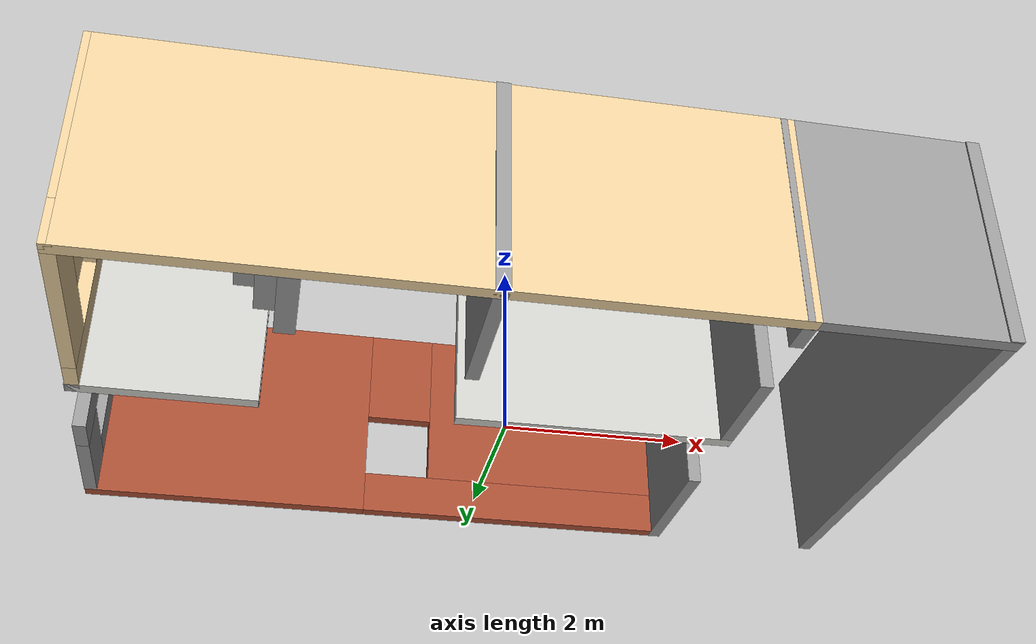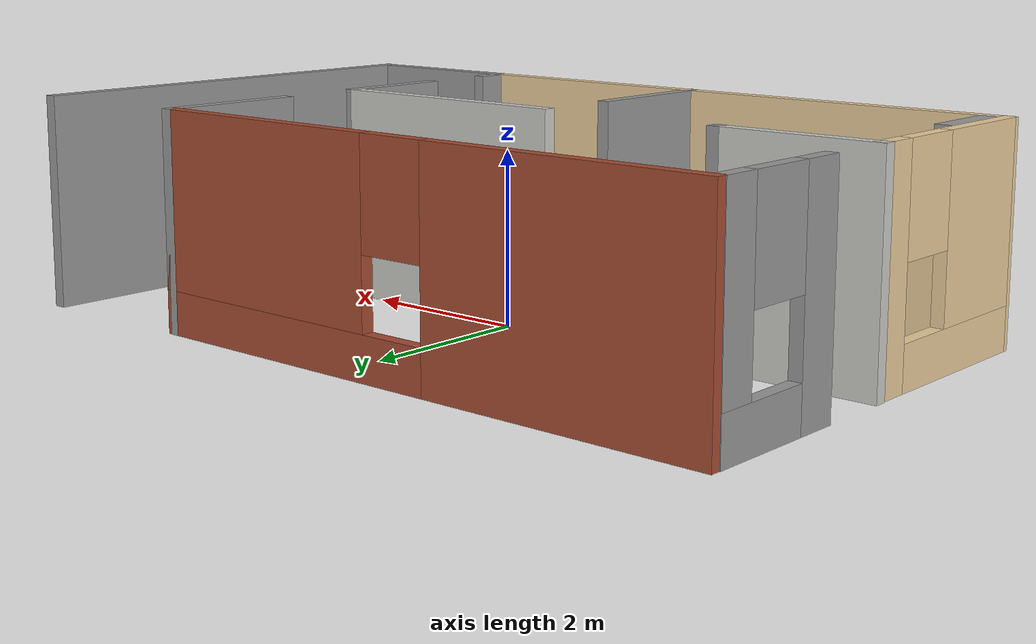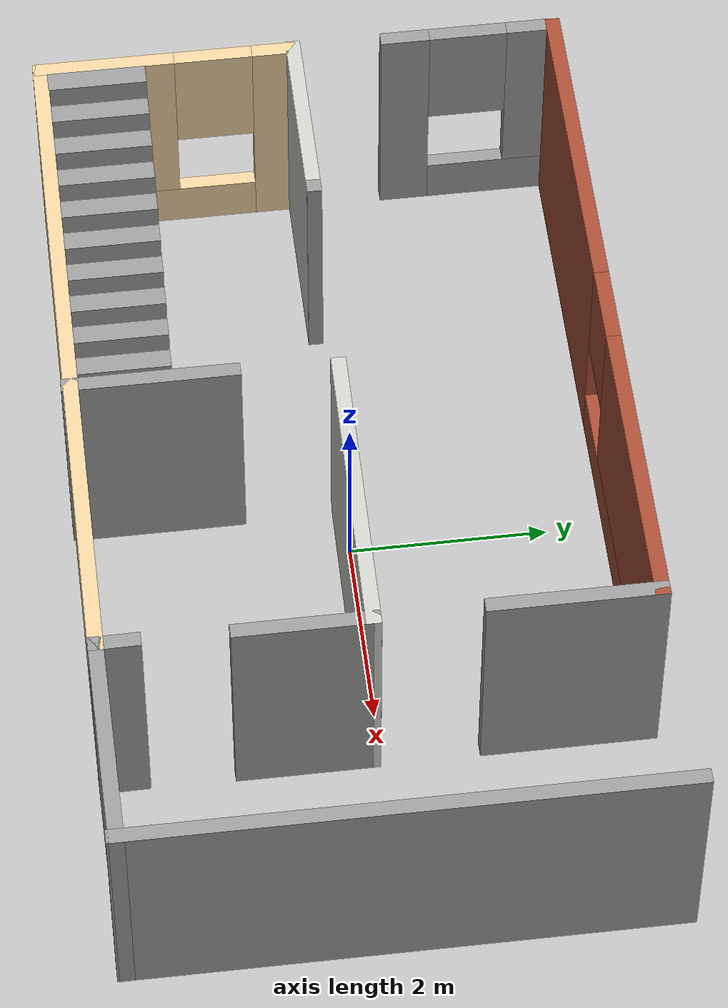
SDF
<?xml version='1.0'?>
<sdf version='1.6'>
  <model name='SLAMHome'>
    <link name='Stairs_1'>
      <pose frame=''>0 0 0 0 -0 0</pose>
      <self_collide>0</self_collide>
      <kinematic>0</kinematic>
      <visual name='Stairs_1_Visual_0'>
        <pose frame=''>-2.48305 -2.07455 0.125 0 0 -1.5708</pose>
        <geometry>
          <box>
            <size>1 0.215239 0.25</size>
          </box>
        </geometry>
        <material>
          <script>
            <uri>file://media/materials/scripts/gazebo.material</uri>
            <name>Gazebo/Grey</name>
          </script>
          <ambient>1 1 1 1</ambient>
          <diffuse>0.7 0.7 0.7 1</diffuse>
          <specular>0.01 0.01 0.01 1</specular>
          <emissive>0 0 0 1</emissive>
        </material>
        <cast_shadows>1</cast_shadows>
        <transparency>0</transparency>
      </visual>
      <visual name='Stairs_1_Visual_1'>
        <pose frame=''>-2.69829 -2.07455 0.375 0 0 -1.5708</pose>
        <geometry>
          <box>
            <size>1 0.215239 0.25</size>
          </box>
        </geometry>
        <material>
          <script>
            <uri>file://media/materials/scripts/gazebo.material</uri>
            <name>Gazebo/Grey</name>
          </script>
          <ambient>1 1 1 1</ambient>
          <diffuse>0.7 0.7 0.7 1</diffuse>
          <specular>0.01 0.01 0.01 1</specular>
          <emissive>0 0 0 1</emissive>
        </material>
        <cast_shadows>1</cast_shadows>
        <transparency>0</transparency>
      </visual>
      <visual name='Stairs_1_Visual_2'>
        <pose frame=''>-2.91353 -2.07455 0.625 0 0 -1.5708</pose>
        <geometry>
          <box>
            <size>1 0.215239 0.25</size>
          </box>
        </geometry>
        <material>
          <script>
            <uri>file://media/materials/scripts/gazebo.material</uri>
            <name>Gazebo/Grey</name>
          </script>
          <ambient>1 1 1 1</ambient>
          <diffuse>0.7 0.7 0.7 1</diffuse>
          <specular>0.01 0.01 0.01 1</specular>
          <emissive>0 0 0 1</emissive>
        </material>
        <cast_shadows>1</cast_shadows>
        <transparency>0</transparency>
      </visual>
      <visual name='Stairs_1_Visual_3'>
        <pose frame=''>-3.12877 -2.07455 0.875 0 0 -1.5708</pose>
        <geometry>
          <box>
            <size>1 0.215239 0.25</size>
          </box>
        </geometry>
        <material>
          <script>
            <uri>file://media/materials/scripts/gazebo.material</uri>
            <name>Gazebo/Grey</name>
          </script>
          <ambient>1 1 1 1</ambient>
          <diffuse>0.7 0.7 0.7 1</diffuse>
          <specular>0.01 0.01 0.01 1</specular>
          <emissive>0 0 0 1</emissive>
        </material>
        <cast_shadows>1</cast_shadows>
        <transparency>0</transparency>
      </visual>
      <visual name='Stairs_1_Visual_4'>
        <pose frame=''>-3.34401 -2.07455 1.125 0 0 -1.5708</pose>
        <geometry>
          <box>
            <size>1 0.215239 0.25</size>
          </box>
        </geometry>
        <material>
          <script>
            <uri>file://media/materials/scripts/gazebo.material</uri>
            <name>Gazebo/Grey</name>
          </script>
          <ambient>1 1 1 1</ambient>
          <diffuse>0.7 0.7 0.7 1</diffuse>
          <specular>0.01 0.01 0.01 1</specular>
          <emissive>0 0 0 1</emissive>
        </material>
        <cast_shadows>1</cast_shadows>
        <transparency>0</transparency>
      </visual>
      <visual name='Stairs_1_Visual_5'>
        <pose frame=''>-3.55925 -2.07455 1.375 0 0 -1.5708</pose>
        <geometry>
          <box>
            <size>1 0.215239 0.25</size>
          </box>
        </geometry>
        <material>
          <script>
            <uri>file://media/materials/scripts/gazebo.material</uri>
            <name>Gazebo/Grey</name>
          </script>
          <ambient>1 1 1 1</ambient>
          <diffuse>0.7 0.7 0.7 1</diffuse>
          <specular>0.01 0.01 0.01 1</specular>
          <emissive>0 0 0 1</emissive>
        </material>
        <cast_shadows>1</cast_shadows>
        <transparency>0</transparency>
      </visual>
      <visual name='Stairs_1_Visual_6'>
        <pose frame=''>-3.77449 -2.07455 1.625 0 0 -1.5708</pose>
        <geometry>
          <box>
            <size>1 0.215239 0.25</size>
          </box>
        </geometry>
        <material>
          <script>
            <uri>file://media/materials/scripts/gazebo.material</uri>
            <name>Gazebo/Grey</name>
          </script>
          <ambient>1 1 1 1</ambient>
          <diffuse>0.7 0.7 0.7 1</diffuse>
          <specular>0.01 0.01 0.01 1</specular>
          <emissive>0 0 0 1</emissive>
        </material>
        <cast_shadows>1</cast_shadows>
        <transparency>0</transparency>
      </visual>
      <visual name='Stairs_1_Visual_7'>
        <pose frame=''>-3.98973 -2.07455 1.875 0 0 -1.5708</pose>
        <geometry>
          <box>
            <size>1 0.215239 0.25</size>
          </box>
        </geometry>
        <material>
          <script>
            <uri>file://media/materials/scripts/gazebo.material</uri>
            <name>Gazebo/Grey</name>
          </script>
          <ambient>1 1 1 1</ambient>
          <diffuse>0.7 0.7 0.7 1</diffuse>
          <specular>0.01 0.01 0.01 1</specular>
          <emissive>0 0 0 1</emissive>
        </material>
        <cast_shadows>1</cast_shadows>
        <transparency>0</transparency>
      </visual>
      <visual name='Stairs_1_Visual_8'>
        <pose frame=''>-4.20497 -2.07455 2.125 0 0 -1.5708</pose>
        <geometry>
          <box>
            <size>1 0.215239 0.25</size>
          </box>
        </geometry>
        <material>
          <script>
            <uri>file://media/materials/scripts/gazebo.material</uri>
            <name>Gazebo/Grey</name>
          </script>
          <ambient>1 1 1 1</ambient>
          <diffuse>0.7 0.7 0.7 1</diffuse>
          <specular>0.01 0.01 0.01 1</specular>
          <emissive>0 0 0 1</emissive>
        </material>
        <cast_shadows>1</cast_shadows>
        <transparency>0</transparency>
      </visual>
      <visual name='Stairs_1_Visual_9'>
        <pose frame=''>-4.42021 -2.07455 2.375 0 0 -1.5708</pose>
        <geometry>
          <box>
            <size>1 0.215239 0.25</size>
          </box>
        </geometry>
        <material>
          <script>
            <uri>file://media/materials/scripts/gazebo.material</uri>
            <name>Gazebo/Grey</name>
          </script>
          <ambient>1 1 1 1</ambient>
          <diffuse>0.7 0.7 0.7 1</diffuse>
          <specular>0.01 0.01 0.01 1</specular>
          <emissive>0 0 0 1</emissive>
        </material>
        <cast_shadows>1</cast_shadows>
        <transparency>0</transparency>
      </visual>
      <collision name='Stairs_1_Collision_1'>
        <laser_retro>0</laser_retro>
        <max_contacts>10</max_contacts>
        <pose frame=''>-2.69829 -2.07455 0.375 0 0 -1.5708</pose>
        <geometry>
          <box>
            <size>1 0.215239 0.25</size>
          </box>
        </geometry>
        <surface>
          <friction>
            <ode>
              <mu>1</mu>
              <mu2>1</mu2>
              <fdir1>0 0 0</fdir1>
              <slip1>0</slip1>
              <slip2>0</slip2>
            </ode>
            <torsional>
              <coefficient>1</coefficient>
              <patch_radius>0</patch_radius>
              <surface_radius>0</surface_radius>
              <use_patch_radius>1</use_patch_radius>
              <ode>
                <slip>0</slip>
              </ode>
            </torsional>
          </friction>
          <bounce>
            <restitution_coefficient>0</restitution_coefficient>
            <threshold>1e+06</threshold>
          </bounce>
          <contact>
            <collide_without_contact>0</collide_without_contact>
            <collide_without_contact_bitmask>1</collide_without_contact_bitmask>
            <collide_bitmask>1</collide_bitmask>
            <ode>
              <soft_cfm>0</soft_cfm>
              <soft_erp>0.2</soft_erp>
              <kp>1e+13</kp>
              <kd>1</kd>
              <max_vel>0.01</max_vel>
              <min_depth>0</min_depth>
            </ode>
            <bullet>
              <split_impulse>1</split_impulse>
              <split_impulse_penetration_threshold>-0.01</split_impulse_penetration_threshold>
              <soft_cfm>0</soft_cfm>
              <soft_erp>0.2</soft_erp>
              <kp>1e+13</kp>
              <kd>1</kd>
            </bullet>
          </contact>
        </surface>
      </collision>
      <collision name='Stairs_1_Collision_0'>
        <laser_retro>0</laser_retro>
        <max_contacts>10</max_contacts>
        <pose frame=''>-2.48305 -2.07455 0.125 0 0 -1.5708</pose>
        <geometry>
          <box>
            <size>1 0.215239 0.25</size>
          </box>
        </geometry>
        <surface>
          <friction>
            <ode>
              <mu>1</mu>
              <mu2>1</mu2>
              <fdir1>0 0 0</fdir1>
              <slip1>0</slip1>
              <slip2>0</slip2>
            </ode>
            <torsional>
              <coefficient>1</coefficient>
              <patch_radius>0</patch_radius>
              <surface_radius>0</surface_radius>
              <use_patch_radius>1</use_patch_radius>
              <ode>
                <slip>0</slip>
              </ode>
            </torsional>
          </friction>
          <bounce>
            <restitution_coefficient>0</restitution_coefficient>
            <threshold>1e+06</threshold>
          </bounce>
          <contact>
            <collide_without_contact>0</collide_without_contact>
            <collide_without_contact_bitmask>1</collide_without_contact_bitmask>
            <collide_bitmask>1</collide_bitmask>
            <ode>
              <soft_cfm>0</soft_cfm>
              <soft_erp>0.2</soft_erp>
              <kp>1e+13</kp>
              <kd>1</kd>
              <max_vel>0.01</max_vel>
              <min_depth>0</min_depth>
            </ode>
            <bullet>
              <split_impulse>1</split_impulse>
              <split_impulse_penetration_threshold>-0.01</split_impulse_penetration_threshold>
              <soft_cfm>0</soft_cfm>
              <soft_erp>0.2</soft_erp>
              <kp>1e+13</kp>
              <kd>1</kd>
            </bullet>
          </contact>
        </surface>
      </collision>
      <collision name='Stairs_1_Collision_2'>
        <laser_retro>0</laser_retro>
        <max_contacts>10</max_contacts>
        <pose frame=''>-2.91353 -2.07455 0.625 0 0 -1.5708</pose>
        <geometry>
          <box>
            <size>1 0.215239 0.25</size>
          </box>
        </geometry>
        <surface>
          <friction>
            <ode>
              <mu>1</mu>
              <mu2>1</mu2>
              <fdir1>0 0 0</fdir1>
              <slip1>0</slip1>
              <slip2>0</slip2>
            </ode>
            <torsional>
              <coefficient>1</coefficient>
              <patch_radius>0</patch_radius>
              <surface_radius>0</surface_radius>
              <use_patch_radius>1</use_patch_radius>
              <ode>
                <slip>0</slip>
              </ode>
            </torsional>
          </friction>
          <bounce>
            <restitution_coefficient>0</restitution_coefficient>
            <threshold>1e+06</threshold>
          </bounce>
          <contact>
            <collide_without_contact>0</collide_without_contact>
            <collide_without_contact_bitmask>1</collide_without_contact_bitmask>
            <collide_bitmask>1</collide_bitmask>
            <ode>
              <soft_cfm>0</soft_cfm>
              <soft_erp>0.2</soft_erp>
              <kp>1e+13</kp>
              <kd>1</kd>
              <max_vel>0.01</max_vel>
              <min_depth>0</min_depth>
            </ode>
            <bullet>
              <split_impulse>1</split_impulse>
              <split_impulse_penetration_threshold>-0.01</split_impulse_penetration_threshold>
              <soft_cfm>0</soft_cfm>
              <soft_erp>0.2</soft_erp>
              <kp>1e+13</kp>
              <kd>1</kd>
            </bullet>
          </contact>
        </surface>
      </collision>
      <collision name='Stairs_1_Collision_3'>
        <laser_retro>0</laser_retro>
        <max_contacts>10</max_contacts>
        <pose frame=''>-3.12877 -2.07455 0.875 0 0 -1.5708</pose>
        <geometry>
          <box>
            <size>1 0.215239 0.25</size>
          </box>
        </geometry>
        <surface>
          <friction>
            <ode>
              <mu>1</mu>
              <mu2>1</mu2>
              <fdir1>0 0 0</fdir1>
              <slip1>0</slip1>
              <slip2>0</slip2>
            </ode>
            <torsional>
              <coefficient>1</coefficient>
              <patch_radius>0</patch_radius>
              <surface_radius>0</surface_radius>
              <use_patch_radius>1</use_patch_radius>
              <ode>
                <slip>0</slip>
              </ode>
            </torsional>
          </friction>
          <bounce>
            <restitution_coefficient>0</restitution_coefficient>
            <threshold>1e+06</threshold>
          </bounce>
          <contact>
            <collide_without_contact>0</collide_without_contact>
            <collide_without_contact_bitmask>1</collide_without_contact_bitmask>
            <collide_bitmask>1</collide_bitmask>
            <ode>
              <soft_cfm>0</soft_cfm>
              <soft_erp>0.2</soft_erp>
              <kp>1e+13</kp>
              <kd>1</kd>
              <max_vel>0.01</max_vel>
              <min_depth>0</min_depth>
            </ode>
            <bullet>
              <split_impulse>1</split_impulse>
              <split_impulse_penetration_threshold>-0.01</split_impulse_penetration_threshold>
              <soft_cfm>0</soft_cfm>
              <soft_erp>0.2</soft_erp>
              <kp>1e+13</kp>
              <kd>1</kd>
            </bullet>
          </contact>
        </surface>
      </collision>
      <collision name='Stairs_1_Collision_4'>
        <laser_retro>0</laser_retro>
        <max_contacts>10</max_contacts>
        <pose frame=''>-3.34401 -2.07455 1.125 0 0 -1.5708</pose>
        <geometry>
          <box>
            <size>1 0.215239 0.25</size>
          </box>
        </geometry>
        <surface>
          <friction>
            <ode>
              <mu>1</mu>
              <mu2>1</mu2>
              <fdir1>0 0 0</fdir1>
              <slip1>0</slip1>
              <slip2>0</slip2>
            </ode>
            <torsional>
              <coefficient>1</coefficient>
              <patch_radius>0</patch_radius>
              <surface_radius>0</surface_radius>
              <use_patch_radius>1</use_patch_radius>
              <ode>
                <slip>0</slip>
              </ode>
            </torsional>
          </friction>
          <bounce>
            <restitution_coefficient>0</restitution_coefficient>
            <threshold>1e+06</threshold>
          </bounce>
          <contact>
            <collide_without_contact>0</collide_without_contact>
            <collide_without_contact_bitmask>1</collide_without_contact_bitmask>
            <collide_bitmask>1</collide_bitmask>
            <ode>
              <soft_cfm>0</soft_cfm>
              <soft_erp>0.2</soft_erp>
              <kp>1e+13</kp>
              <kd>1</kd>
              <max_vel>0.01</max_vel>
              <min_depth>0</min_depth>
            </ode>
            <bullet>
              <split_impulse>1</split_impulse>
              <split_impulse_penetration_threshold>-0.01</split_impulse_penetration_threshold>
              <soft_cfm>0</soft_cfm>
              <soft_erp>0.2</soft_erp>
              <kp>1e+13</kp>
              <kd>1</kd>
            </bullet>
          </contact>
        </surface>
      </collision>
      <collision name='Stairs_1_Collision_7'>
        <laser_retro>0</laser_retro>
        <max_contacts>10</max_contacts>
        <pose frame=''>-3.98973 -2.07455 1.875 0 0 -1.5708</pose>
        <geometry>
          <box>
            <size>1 0.215239 0.25</size>
          </box>
        </geometry>
        <surface>
          <friction>
            <ode>
              <mu>1</mu>
              <mu2>1</mu2>
              <fdir1>0 0 0</fdir1>
              <slip1>0</slip1>
              <slip2>0</slip2>
            </ode>
            <torsional>
              <coefficient>1</coefficient>
              <patch_radius>0</patch_radius>
              <surface_radius>0</surface_radius>
              <use_patch_radius>1</use_patch_radius>
              <ode>
                <slip>0</slip>
              </ode>
            </torsional>
          </friction>
          <bounce>
            <restitution_coefficient>0</restitution_coefficient>
            <threshold>1e+06</threshold>
          </bounce>
          <contact>
            <collide_without_contact>0</collide_without_contact>
            <collide_without_contact_bitmask>1</collide_without_contact_bitmask>
            <collide_bitmask>1</collide_bitmask>
            <ode>
              <soft_cfm>0</soft_cfm>
              <soft_erp>0.2</soft_erp>
              <kp>1e+13</kp>
              <kd>1</kd>
              <max_vel>0.01</max_vel>
              <min_depth>0</min_depth>
            </ode>
            <bullet>
              <split_impulse>1</split_impulse>
              <split_impulse_penetration_threshold>-0.01</split_impulse_penetration_threshold>
              <soft_cfm>0</soft_cfm>
              <soft_erp>0.2</soft_erp>
              <kp>1e+13</kp>
              <kd>1</kd>
            </bullet>
          </contact>
        </surface>
      </collision>
      <collision name='Stairs_1_Collision_5'>
        <laser_retro>0</laser_retro>
        <max_contacts>10</max_contacts>
        <pose frame=''>-3.55925 -2.07455 1.375 0 0 -1.5708</pose>
        <geometry>
          <box>
            <size>1 0.215239 0.25</size>
          </box>
        </geometry>
        <surface>
          <friction>
            <ode>
              <mu>1</mu>
              <mu2>1</mu2>
              <fdir1>0 0 0</fdir1>
              <slip1>0</slip1>
              <slip2>0</slip2>
            </ode>
            <torsional>
              <coefficient>1</coefficient>
              <patch_radius>0</patch_radius>
              <surface_radius>0</surface_radius>
              <use_patch_radius>1</use_patch_radius>
              <ode>
                <slip>0</slip>
              </ode>
            </torsional>
          </friction>
          <bounce>
            <restitution_coefficient>0</restitution_coefficient>
            <threshold>1e+06</threshold>
          </bounce>
          <contact>
            <collide_without_contact>0</collide_without_contact>
            <collide_without_contact_bitmask>1</collide_without_contact_bitmask>
            <collide_bitmask>1</collide_bitmask>
            <ode>
              <soft_cfm>0</soft_cfm>
              <soft_erp>0.2</soft_erp>
              <kp>1e+13</kp>
              <kd>1</kd>
              <max_vel>0.01</max_vel>
              <min_depth>0</min_depth>
            </ode>
            <bullet>
              <split_impulse>1</split_impulse>
              <split_impulse_penetration_threshold>-0.01</split_impulse_penetration_threshold>
              <soft_cfm>0</soft_cfm>
              <soft_erp>0.2</soft_erp>
              <kp>1e+13</kp>
              <kd>1</kd>
            </bullet>
          </contact>
        </surface>
      </collision>
      <collision name='Stairs_1_Collision_6'>
        <laser_retro>0</laser_retro>
        <max_contacts>10</max_contacts>
        <pose frame=''>-3.77449 -2.07455 1.625 0 0 -1.5708</pose>
        <geometry>
          <box>
            <size>1 0.215239 0.25</size>
          </box>
        </geometry>
        <surface>
          <friction>
            <ode>
              <mu>1</mu>
              <mu2>1</mu2>
              <fdir1>0 0 0</fdir1>
              <slip1>0</slip1>
              <slip2>0</slip2>
            </ode>
            <torsional>
              <coefficient>1</coefficient>
              <patch_radius>0</patch_radius>
              <surface_radius>0</surface_radius>
              <use_patch_radius>1</use_patch_radius>
              <ode>
                <slip>0</slip>
              </ode>
            </torsional>
          </friction>
          <bounce>
            <restitution_coefficient>0</restitution_coefficient>
            <threshold>1e+06</threshold>
          </bounce>
          <contact>
            <collide_without_contact>0</collide_without_contact>
            <collide_without_contact_bitmask>1</collide_without_contact_bitmask>
            <collide_bitmask>1</collide_bitmask>
            <ode>
              <soft_cfm>0</soft_cfm>
              <soft_erp>0.2</soft_erp>
              <kp>1e+13</kp>
              <kd>1</kd>
              <max_vel>0.01</max_vel>
              <min_depth>0</min_depth>
            </ode>
            <bullet>
              <split_impulse>1</split_impulse>
              <split_impulse_penetration_threshold>-0.01</split_impulse_penetration_threshold>
              <soft_cfm>0</soft_cfm>
              <soft_erp>0.2</soft_erp>
              <kp>1e+13</kp>
              <kd>1</kd>
            </bullet>
          </contact>
        </surface>
      </collision>
      <collision name='Stairs_1_Collision_8'>
        <laser_retro>0</laser_retro>
        <max_contacts>10</max_contacts>
        <pose frame=''>-4.20497 -2.07455 2.125 0 0 -1.5708</pose>
        <geometry>
          <box>
            <size>1 0.215239 0.25</size>
          </box>
        </geometry>
        <surface>
          <friction>
            <ode>
              <mu>1</mu>
              <mu2>1</mu2>
              <fdir1>0 0 0</fdir1>
              <slip1>0</slip1>
              <slip2>0</slip2>
            </ode>
            <torsional>
              <coefficient>1</coefficient>
              <patch_radius>0</patch_radius>
              <surface_radius>0</surface_radius>
              <use_patch_radius>1</use_patch_radius>
              <ode>
                <slip>0</slip>
              </ode>
            </torsional>
          </friction>
          <bounce>
            <restitution_coefficient>0</restitution_coefficient>
            <threshold>1e+06</threshold>
          </bounce>
          <contact>
            <collide_without_contact>0</collide_without_contact>
            <collide_without_contact_bitmask>1</collide_without_contact_bitmask>
            <collide_bitmask>1</collide_bitmask>
            <ode>
              <soft_cfm>0</soft_cfm>
              <soft_erp>0.2</soft_erp>
              <kp>1e+13</kp>
              <kd>1</kd>
              <max_vel>0.01</max_vel>
              <min_depth>0</min_depth>
            </ode>
            <bullet>
              <split_impulse>1</split_impulse>
              <split_impulse_penetration_threshold>-0.01</split_impulse_penetration_threshold>
              <soft_cfm>0</soft_cfm>
              <soft_erp>0.2</soft_erp>
              <kp>1e+13</kp>
              <kd>1</kd>
            </bullet>
          </contact>
        </surface>
      </collision>
      <collision name='Stairs_1_Collision_9'>
        <laser_retro>0</laser_retro>
        <max_contacts>10</max_contacts>
        <pose frame=''>-4.42021 -2.07455 2.375 0 0 -1.5708</pose>
        <geometry>
          <box>
            <size>1 0.215239 0.25</size>
          </box>
        </geometry>
        <surface>
          <friction>
            <ode>
              <mu>1</mu>
              <mu2>1</mu2>
              <fdir1>0 0 0</fdir1>
              <slip1>0</slip1>
              <slip2>0</slip2>
            </ode>
            <torsional>
              <coefficient>1</coefficient>
              <patch_radius>0</patch_radius>
              <surface_radius>0</surface_radius>
              <use_patch_radius>1</use_patch_radius>
              <ode>
                <slip>0</slip>
              </ode>
            </torsional>
          </friction>
          <bounce>
            <restitution_coefficient>0</restitution_coefficient>
            <threshold>1e+06</threshold>
          </bounce>
          <contact>
            <collide_without_contact>0</collide_without_contact>
            <collide_without_contact_bitmask>1</collide_without_contact_bitmask>
            <collide_bitmask>1</collide_bitmask>
            <ode>
              <soft_cfm>0</soft_cfm>
              <soft_erp>0.2</soft_erp>
              <kp>1e+13</kp>
              <kd>1</kd>
              <max_vel>0.01</max_vel>
              <min_depth>0</min_depth>
            </ode>
            <bullet>
              <split_impulse>1</split_impulse>
              <split_impulse_penetration_threshold>-0.01</split_impulse_penetration_threshold>
              <soft_cfm>0</soft_cfm>
              <soft_erp>0.2</soft_erp>
              <kp>1e+13</kp>
              <kd>1</kd>
            </bullet>
          </contact>
        </surface>
      </collision>
    </link>
    <link name='Wall_1'>
      <pose frame=''>-2.74721 -0.041047 0 0 -0 0</pose>
      <self_collide>0</self_collide>
      <kinematic>0</kinematic>
      <visual name='Wall_1_Visual'>
        <pose frame=''>0 0 1.25 0 -0 0</pose>
        <geometry>
          <box>
            <size>0.15 0.15 2.5</size>
          </box>
        </geometry>
        <material>
          <script>
            <uri>file://media/materials/scripts/gazebo.material</uri>
            <name>Gazebo/Grey</name>
          </script>
          <ambient>1 1 1 1</ambient>
          <diffuse>0.7 0.7 0.7 1</diffuse>
          <specular>0.01 0.01 0.01 1</specular>
          <emissive>0 0 0 1</emissive>
        </material>
        <cast_shadows>1</cast_shadows>
        <transparency>0</transparency>
      </visual>
      <collision name='Wall_1_Collision'>
        <laser_retro>0</laser_retro>
        <max_contacts>10</max_contacts>
        <pose frame=''>0 0 1.25 0 -0 0</pose>
        <geometry>
          <box>
            <size>0.15 0.15 2.5</size>
          </box>
        </geometry>
        <surface>
          <friction>
            <ode>
              <mu>1</mu>
              <mu2>1</mu2>
              <fdir1>0 0 0</fdir1>
              <slip1>0</slip1>
              <slip2>0</slip2>
            </ode>
            <torsional>
              <coefficient>1</coefficient>
              <patch_radius>0</patch_radius>
              <surface_radius>0</surface_radius>
              <use_patch_radius>1</use_patch_radius>
              <ode>
                <slip>0</slip>
              </ode>
            </torsional>
          </friction>
          <bounce>
            <restitution_coefficient>0</restitution_coefficient>
            <threshold>1e+06</threshold>
          </bounce>
          <contact>
            <collide_without_contact>0</collide_without_contact>
            <collide_without_contact_bitmask>1</collide_without_contact_bitmask>
            <collide_bitmask>1</collide_bitmask>
            <ode>
              <soft_cfm>0</soft_cfm>
              <soft_erp>0.2</soft_erp>
              <kp>1e+13</kp>
              <kd>1</kd>
              <max_vel>0.01</max_vel>
              <min_depth>0</min_depth>
            </ode>
            <bullet>
              <split_impulse>1</split_impulse>
              <split_impulse_penetration_threshold>-0.01</split_impulse_penetration_threshold>
              <soft_cfm>0</soft_cfm>
              <soft_erp>0.2</soft_erp>
              <kp>1e+13</kp>
              <kd>1</kd>
            </bullet>
          </contact>
        </surface>
      </collision>
    </link>
    <link name='Wall_13'>
      <pose frame=''>-4.59721 -0.041047 0 0 -0 0</pose>
      <self_collide>0</self_collide>
      <kinematic>0</kinematic>
      <visual name='Wall_13_Visual'>
        <pose frame=''>0 0 1.25 0 -0 0</pose>
        <geometry>
          <box>
            <size>0.15 0.15 2.5</size>
          </box>
        </geometry>
        <material>
          <script>
            <uri>file://media/materials/scripts/gazebo.material</uri>
            <name>Gazebo/Grey</name>
          </script>
          <ambient>1 1 1 1</ambient>
          <diffuse>0.7 0.7 0.7 1</diffuse>
          <specular>0.01 0.01 0.01 1</specular>
          <emissive>0 0 0 1</emissive>
        </material>
        <cast_shadows>1</cast_shadows>
        <transparency>0</transparency>
      </visual>
      <collision name='Wall_13_Collision'>
        <laser_retro>0</laser_retro>
        <max_contacts>10</max_contacts>
        <pose frame=''>0 0 1.25 0 -0 0</pose>
        <geometry>
          <box>
            <size>0.15 0.15 2.5</size>
          </box>
        </geometry>
        <surface>
          <friction>
            <ode>
              <mu>1</mu>
              <mu2>1</mu2>
              <fdir1>0 0 0</fdir1>
              <slip1>0</slip1>
              <slip2>0</slip2>
            </ode>
            <torsional>
              <coefficient>1</coefficient>
              <patch_radius>0</patch_radius>
              <surface_radius>0</surface_radius>
              <use_patch_radius>1</use_patch_radius>
              <ode>
                <slip>0</slip>
              </ode>
            </torsional>
          </friction>
          <bounce>
            <restitution_coefficient>0</restitution_coefficient>
            <threshold>1e+06</threshold>
          </bounce>
          <contact>
            <collide_without_contact>0</collide_without_contact>
            <collide_without_contact_bitmask>1</collide_without_contact_bitmask>
            <collide_bitmask>1</collide_bitmask>
            <ode>
              <soft_cfm>0</soft_cfm>
              <soft_erp>0.2</soft_erp>
              <kp>1e+13</kp>
              <kd>1</kd>
              <max_vel>0.01</max_vel>
              <min_depth>0</min_depth>
            </ode>
            <bullet>
              <split_impulse>1</split_impulse>
              <split_impulse_penetration_threshold>-0.01</split_impulse_penetration_threshold>
              <soft_cfm>0</soft_cfm>
              <soft_erp>0.2</soft_erp>
              <kp>1e+13</kp>
              <kd>1</kd>
            </bullet>
          </contact>
        </surface>
      </collision>
    </link>
    <link name='Wall_15'>
      <pose frame=''>-4.59721 -1.34105 0 0 0 -1.5708</pose>
      <self_collide>0</self_collide>
      <kinematic>0</kinematic>
      <visual name='Wall_15_Visual_1'>
        <pose frame=''>0.252997 0 0.25 0 -0 0</pose>
        <geometry>
          <box>
            <size>2.24401 0.15 0.5</size>
          </box>
        </geometry>
        <material>
          <script>
            <uri>file://media/materials/scripts/gazebo.material</uri>
            <name>Gazebo/Grey</name>
          </script>
          <ambient>0.921569 0.807843 0.615686 1</ambient>
          <diffuse>0.7 0.7 0.7 1</diffuse>
          <specular>0.01 0.01 0.01 1</specular>
          <emissive>0 0 0 1</emissive>
        </material>
        <cast_shadows>1</cast_shadows>
        <transparency>0</transparency>
      </visual>
      <visual name='Wall_15_Visual_0'>
        <pose frame=''>-1.122 0 1.25 0 -0 0</pose>
        <geometry>
          <box>
            <size>0.505993 0.15 2.5</size>
          </box>
        </geometry>
        <material>
          <script>
            <uri>file://media/materials/scripts/gazebo.material</uri>
            <name>Gazebo/Grey</name>
          </script>
          <ambient>0.921569 0.807843 0.615686 1</ambient>
          <diffuse>0.7 0.7 0.7 1</diffuse>
          <specular>0.01 0.01 0.01 1</specular>
          <emissive>0 0 0 1</emissive>
        </material>
        <cast_shadows>1</cast_shadows>
        <transparency>0</transparency>
      </visual>
      <visual name='Wall_15_Visual_2'>
        <pose frame=''>0.652997 0 1.5 0 -0 0</pose>
        <geometry>
          <box>
            <size>1.44401 0.15 2</size>
          </box>
        </geometry>
        <material>
          <script>
            <uri>file://media/materials/scripts/gazebo.material</uri>
            <name>Gazebo/Grey</name>
          </script>
          <ambient>0.921569 0.807843 0.615686 1</ambient>
          <diffuse>0.7 0.7 0.7 1</diffuse>
          <specular>0.01 0.01 0.01 1</specular>
          <emissive>0 0 0 1</emissive>
        </material>
        <cast_shadows>1</cast_shadows>
        <transparency>0</transparency>
      </visual>
      <visual name='Wall_15_Visual_3'>
        <pose frame=''>-0.469007 0 1.9 0 -0 0</pose>
        <geometry>
          <box>
            <size>0.8 0.15 1.2</size>
          </box>
        </geometry>
        <material>
          <script>
            <uri>file://media/materials/scripts/gazebo.material</uri>
            <name>Gazebo/Grey</name>
          </script>
          <ambient>0.921569 0.807843 0.615686 1</ambient>
          <diffuse>0.7 0.7 0.7 1</diffuse>
          <specular>0.01 0.01 0.01 1</specular>
          <emissive>0 0 0 1</emissive>
        </material>
        <cast_shadows>1</cast_shadows>
        <transparency>0</transparency>
      </visual>
      <collision name='Wall_15_Collision_0'>
        <laser_retro>0</laser_retro>
        <max_contacts>10</max_contacts>
        <pose frame=''>-1.122 0 1.25 0 -0 0</pose>
        <geometry>
          <box>
            <size>0.505993 0.15 2.5</size>
          </box>
        </geometry>
        <surface>
          <friction>
            <ode>
              <mu>1</mu>
              <mu2>1</mu2>
              <fdir1>0 0 0</fdir1>
              <slip1>0</slip1>
              <slip2>0</slip2>
            </ode>
            <torsional>
              <coefficient>1</coefficient>
              <patch_radius>0</patch_radius>
              <surface_radius>0</surface_radius>
              <use_patch_radius>1</use_patch_radius>
              <ode>
                <slip>0</slip>
              </ode>
            </torsional>
          </friction>
          <bounce>
            <restitution_coefficient>0</restitution_coefficient>
            <threshold>1e+06</threshold>
          </bounce>
          <contact>
            <collide_without_contact>0</collide_without_contact>
            <collide_without_contact_bitmask>1</collide_without_contact_bitmask>
            <collide_bitmask>1</collide_bitmask>
            <ode>
              <soft_cfm>0</soft_cfm>
              <soft_erp>0.2</soft_erp>
              <kp>1e+13</kp>
              <kd>1</kd>
              <max_vel>0.01</max_vel>
              <min_depth>0</min_depth>
            </ode>
            <bullet>
              <split_impulse>1</split_impulse>
              <split_impulse_penetration_threshold>-0.01</split_impulse_penetration_threshold>
              <soft_cfm>0</soft_cfm>
              <soft_erp>0.2</soft_erp>
              <kp>1e+13</kp>
              <kd>1</kd>
            </bullet>
          </contact>
        </surface>
      </collision>
      <collision name='Wall_15_Collision_2'>
        <laser_retro>0</laser_retro>
        <max_contacts>10</max_contacts>
        <pose frame=''>0.652997 0 1.5 0 -0 0</pose>
        <geometry>
          <box>
            <size>1.44401 0.15 2</size>
          </box>
        </geometry>
        <surface>
          <friction>
            <ode>
              <mu>1</mu>
              <mu2>1</mu2>
              <fdir1>0 0 0</fdir1>
              <slip1>0</slip1>
              <slip2>0</slip2>
            </ode>
            <torsional>
              <coefficient>1</coefficient>
              <patch_radius>0</patch_radius>
              <surface_radius>0</surface_radius>
              <use_patch_radius>1</use_patch_radius>
              <ode>
                <slip>0</slip>
              </ode>
            </torsional>
          </friction>
          <bounce>
            <restitution_coefficient>0</restitution_coefficient>
            <threshold>1e+06</threshold>
          </bounce>
          <contact>
            <collide_without_contact>0</collide_without_contact>
            <collide_without_contact_bitmask>1</collide_without_contact_bitmask>
            <collide_bitmask>1</collide_bitmask>
            <ode>
              <soft_cfm>0</soft_cfm>
              <soft_erp>0.2</soft_erp>
              <kp>1e+13</kp>
              <kd>1</kd>
              <max_vel>0.01</max_vel>
              <min_depth>0</min_depth>
            </ode>
            <bullet>
              <split_impulse>1</split_impulse>
              <split_impulse_penetration_threshold>-0.01</split_impulse_penetration_threshold>
              <soft_cfm>0</soft_cfm>
              <soft_erp>0.2</soft_erp>
              <kp>1e+13</kp>
              <kd>1</kd>
            </bullet>
          </contact>
        </surface>
      </collision>
      <collision name='Wall_15_Collision_1'>
        <laser_retro>0</laser_retro>
        <max_contacts>10</max_contacts>
        <pose frame=''>0.252997 0 0.25 0 -0 0</pose>
        <geometry>
          <box>
            <size>2.24401 0.15 0.5</size>
          </box>
        </geometry>
        <surface>
          <friction>
            <ode>
              <mu>1</mu>
              <mu2>1</mu2>
              <fdir1>0 0 0</fdir1>
              <slip1>0</slip1>
              <slip2>0</slip2>
            </ode>
            <torsional>
              <coefficient>1</coefficient>
              <patch_radius>0</patch_radius>
              <surface_radius>0</surface_radius>
              <use_patch_radius>1</use_patch_radius>
              <ode>
                <slip>0</slip>
              </ode>
            </torsional>
          </friction>
          <bounce>
            <restitution_coefficient>0</restitution_coefficient>
            <threshold>1e+06</threshold>
          </bounce>
          <contact>
            <collide_without_contact>0</collide_without_contact>
            <collide_without_contact_bitmask>1</collide_without_contact_bitmask>
            <collide_bitmask>1</collide_bitmask>
            <ode>
              <soft_cfm>0</soft_cfm>
              <soft_erp>0.2</soft_erp>
              <kp>1e+13</kp>
              <kd>1</kd>
              <max_vel>0.01</max_vel>
              <min_depth>0</min_depth>
            </ode>
            <bullet>
              <split_impulse>1</split_impulse>
              <split_impulse_penetration_threshold>-0.01</split_impulse_penetration_threshold>
              <soft_cfm>0</soft_cfm>
              <soft_erp>0.2</soft_erp>
              <kp>1e+13</kp>
              <kd>1</kd>
            </bullet>
          </contact>
        </surface>
      </collision>
      <collision name='Wall_15_Collision_3'>
        <laser_retro>0</laser_retro>
        <max_contacts>10</max_contacts>
        <pose frame=''>-0.469007 0 1.9 0 -0 0</pose>
        <geometry>
          <box>
            <size>0.8 0.15 1.2</size>
          </box>
        </geometry>
        <surface>
          <friction>
            <ode>
              <mu>1</mu>
              <mu2>1</mu2>
              <fdir1>0 0 0</fdir1>
              <slip1>0</slip1>
              <slip2>0</slip2>
            </ode>
            <torsional>
              <coefficient>1</coefficient>
              <patch_radius>0</patch_radius>
              <surface_radius>0</surface_radius>
              <use_patch_radius>1</use_patch_radius>
              <ode>
                <slip>0</slip>
              </ode>
            </torsional>
          </friction>
          <bounce>
            <restitution_coefficient>0</restitution_coefficient>
            <threshold>1e+06</threshold>
          </bounce>
          <contact>
            <collide_without_contact>0</collide_without_contact>
            <collide_without_contact_bitmask>1</collide_without_contact_bitmask>
            <collide_bitmask>1</collide_bitmask>
            <ode>
              <soft_cfm>0</soft_cfm>
              <soft_erp>0.2</soft_erp>
              <kp>1e+13</kp>
              <kd>1</kd>
              <max_vel>0.01</max_vel>
              <min_depth>0</min_depth>
            </ode>
            <bullet>
              <split_impulse>1</split_impulse>
              <split_impulse_penetration_threshold>-0.01</split_impulse_penetration_threshold>
              <soft_cfm>0</soft_cfm>
              <soft_erp>0.2</soft_erp>
              <kp>1e+13</kp>
              <kd>1</kd>
            </bullet>
          </contact>
        </surface>
      </collision>
    </link>
    <link name='Wall_16'>
      <pose frame=''>-1.04721 -2.66116 0 0 0 -0.005666</pose>
      <self_collide>0</self_collide>
      <kinematic>0</kinematic>
      <visual name='Wall_16_Visual'>
        <pose frame=''>0 0 1.25 0 -0 0</pose>
        <geometry>
          <box>
            <size>7.25 0.15 2.5</size>
          </box>
        </geometry>
        <material>
          <script>
            <uri>file://media/materials/scripts/gazebo.material</uri>
            <name>Gazebo/Grey</name>
          </script>
          <ambient>0.921569 0.807843 0.615686 1</ambient>
          <diffuse>0.7 0.7 0.7 1</diffuse>
          <specular>0.01 0.01 0.01 1</specular>
          <emissive>0 0 0 1</emissive>
        </material>
        <cast_shadows>1</cast_shadows>
        <transparency>0</transparency>
      </visual>
      <collision name='Wall_16_Collision'>
        <laser_retro>0</laser_retro>
        <max_contacts>10</max_contacts>
        <pose frame=''>0 0 1.25 0 -0 0</pose>
        <geometry>
          <box>
            <size>7.25 0.15 2.5</size>
          </box>
        </geometry>
        <surface>
          <friction>
            <ode>
              <mu>1</mu>
              <mu2>1</mu2>
              <fdir1>0 0 0</fdir1>
              <slip1>0</slip1>
              <slip2>0</slip2>
            </ode>
            <torsional>
              <coefficient>1</coefficient>
              <patch_radius>0</patch_radius>
              <surface_radius>0</surface_radius>
              <use_patch_radius>1</use_patch_radius>
              <ode>
                <slip>0</slip>
              </ode>
            </torsional>
          </friction>
          <bounce>
            <restitution_coefficient>0</restitution_coefficient>
            <threshold>1e+06</threshold>
          </bounce>
          <contact>
            <collide_without_contact>0</collide_without_contact>
            <collide_without_contact_bitmask>1</collide_without_contact_bitmask>
            <collide_bitmask>1</collide_bitmask>
            <ode>
              <soft_cfm>0</soft_cfm>
              <soft_erp>0.2</soft_erp>
              <kp>1e+13</kp>
              <kd>1</kd>
              <max_vel>0.01</max_vel>
              <min_depth>0</min_depth>
            </ode>
            <bullet>
              <split_impulse>1</split_impulse>
              <split_impulse_penetration_threshold>-0.01</split_impulse_penetration_threshold>
              <soft_cfm>0</soft_cfm>
              <soft_erp>0.2</soft_erp>
              <kp>1e+13</kp>
              <kd>1</kd>
            </bullet>
          </contact>
        </surface>
      </collision>
    </link>
    <link name='Wall_18'>
      <pose frame=''>2.51279 -0.716048 0 0 0 -1.5708</pose>
      <self_collide>0</self_collide>
      <kinematic>0</kinematic>
      <visual name='Wall_18_Visual'>
        <pose frame=''>0 0 1.25 0 -0 0</pose>
        <geometry>
          <box>
            <size>1.42 0.15 2.5</size>
          </box>
        </geometry>
        <material>
          <script>
            <uri>file://media/materials/scripts/gazebo.material</uri>
            <name>Gazebo/Grey</name>
          </script>
          <ambient>1 1 1 1</ambient>
          <diffuse>0.7 0.7 0.7 1</diffuse>
          <specular>0.01 0.01 0.01 1</specular>
          <emissive>0 0 0 1</emissive>
        </material>
        <cast_shadows>1</cast_shadows>
        <transparency>0</transparency>
      </visual>
      <collision name='Wall_18_Collision'>
        <laser_retro>0</laser_retro>
        <max_contacts>10</max_contacts>
        <pose frame=''>0 0 1.25 0 -0 0</pose>
        <geometry>
          <box>
            <size>1.42 0.15 2.5</size>
          </box>
        </geometry>
        <surface>
          <friction>
            <ode>
              <mu>1</mu>
              <mu2>1</mu2>
              <fdir1>0 0 0</fdir1>
              <slip1>0</slip1>
              <slip2>0</slip2>
            </ode>
            <torsional>
              <coefficient>1</coefficient>
              <patch_radius>0</patch_radius>
              <surface_radius>0</surface_radius>
              <use_patch_radius>1</use_patch_radius>
              <ode>
                <slip>0</slip>
              </ode>
            </torsional>
          </friction>
          <bounce>
            <restitution_coefficient>0</restitution_coefficient>
            <threshold>1e+06</threshold>
          </bounce>
          <contact>
            <collide_without_contact>0</collide_without_contact>
            <collide_without_contact_bitmask>1</collide_without_contact_bitmask>
            <collide_bitmask>1</collide_bitmask>
            <ode>
              <soft_cfm>0</soft_cfm>
              <soft_erp>0.2</soft_erp>
              <kp>1e+13</kp>
              <kd>1</kd>
              <max_vel>0.01</max_vel>
              <min_depth>0</min_depth>
            </ode>
            <bullet>
              <split_impulse>1</split_impulse>
              <split_impulse_penetration_threshold>-0.01</split_impulse_penetration_threshold>
              <soft_cfm>0</soft_cfm>
              <soft_erp>0.2</soft_erp>
              <kp>1e+13</kp>
              <kd>1</kd>
            </bullet>
          </contact>
        </surface>
      </collision>
    </link>
    <link name='Wall_2'>
      <pose frame=''>-3.68221 -0.041047 0 0 -0 3.14159</pose>
      <self_collide>0</self_collide>
      <kinematic>0</kinematic>
      <visual name='Wall_2_Visual'>
        <pose frame=''>0 0 1.25 0 -0 0</pose>
        <geometry>
          <box>
            <size>2 0.15 2.5</size>
          </box>
        </geometry>
        <material>
          <script>
            <uri>file://media/materials/scripts/gazebo.material</uri>
            <name>Gazebo/CeilingTiled</name>
          </script>
          <ambient>1 1 1 1</ambient>
          <diffuse>1 1 1 1</diffuse>
          <specular>0 0 0 1</specular>
          <emissive>0 0 0 1</emissive>
        </material>
        <cast_shadows>1</cast_shadows>
        <transparency>0</transparency>
      </visual>
      <collision name='Wall_2_Collision'>
        <laser_retro>0</laser_retro>
        <max_contacts>10</max_contacts>
        <pose frame=''>0 0 1.25 0 -0 0</pose>
        <geometry>
          <box>
            <size>2 0.15 2.5</size>
          </box>
        </geometry>
        <surface>
          <friction>
            <ode>
              <mu>1</mu>
              <mu2>1</mu2>
              <fdir1>0 0 0</fdir1>
              <slip1>0</slip1>
              <slip2>0</slip2>
            </ode>
            <torsional>
              <coefficient>1</coefficient>
              <patch_radius>0</patch_radius>
              <surface_radius>0</surface_radius>
              <use_patch_radius>1</use_patch_radius>
              <ode>
                <slip>0</slip>
              </ode>
            </torsional>
          </friction>
          <bounce>
            <restitution_coefficient>0</restitution_coefficient>
            <threshold>1e+06</threshold>
          </bounce>
          <contact>
            <collide_without_contact>0</collide_without_contact>
            <collide_without_contact_bitmask>1</collide_without_contact_bitmask>
            <collide_bitmask>1</collide_bitmask>
            <ode>
              <soft_cfm>0</soft_cfm>
              <soft_erp>0.2</soft_erp>
              <kp>1e+13</kp>
              <kd>1</kd>
              <max_vel>0.01</max_vel>
              <min_depth>0</min_depth>
            </ode>
            <bullet>
              <split_impulse>1</split_impulse>
              <split_impulse_penetration_threshold>-0.01</split_impulse_penetration_threshold>
              <soft_cfm>0</soft_cfm>
              <soft_erp>0.2</soft_erp>
              <kp>1e+13</kp>
              <kd>1</kd>
            </bullet>
          </contact>
        </surface>
      </collision>
    </link>
    <link name='Wall_21'>
      <pose frame=''>4.60664 0 0 0 0 -1.5708</pose>
      <self_collide>0</self_collide>
      <kinematic>0</kinematic>
      <visual name='Wall_21_Visual'>
        <pose frame=''>0 0 1.25 0 -0 0</pose>
        <geometry>
          <box>
            <size>5.54023 0.15 2.5</size>
          </box>
        </geometry>
        <material>
          <script>
            <uri>file://media/materials/scripts/gazebo.material</uri>
            <name>Gazebo/Grey</name>
          </script>
          <ambient>1 1 1 1</ambient>
          <diffuse>0.7 0.7 0.7 1</diffuse>
          <specular>0.01 0.01 0.01 1</specular>
          <emissive>0 0 0 1</emissive>
        </material>
        <cast_shadows>1</cast_shadows>
        <transparency>0</transparency>
      </visual>
      <collision name='Wall_21_Collision'>
        <laser_retro>0</laser_retro>
        <max_contacts>10</max_contacts>
        <pose frame=''>0 0 1.25 0 -0 0</pose>
        <geometry>
          <box>
            <size>5.54023 0.15 2.5</size>
          </box>
        </geometry>
        <surface>
          <friction>
            <ode>
              <mu>1</mu>
              <mu2>1</mu2>
              <fdir1>0 0 0</fdir1>
              <slip1>0</slip1>
              <slip2>0</slip2>
            </ode>
            <torsional>
              <coefficient>1</coefficient>
              <patch_radius>0</patch_radius>
              <surface_radius>0</surface_radius>
              <use_patch_radius>1</use_patch_radius>
              <ode>
                <slip>0</slip>
              </ode>
            </torsional>
          </friction>
          <bounce>
            <restitution_coefficient>0</restitution_coefficient>
            <threshold>1e+06</threshold>
          </bounce>
          <contact>
            <collide_without_contact>0</collide_without_contact>
            <collide_without_contact_bitmask>1</collide_without_contact_bitmask>
            <collide_bitmask>1</collide_bitmask>
            <ode>
              <soft_cfm>0</soft_cfm>
              <soft_erp>0.2</soft_erp>
              <kp>1e+13</kp>
              <kd>1</kd>
              <max_vel>0.01</max_vel>
              <min_depth>0</min_depth>
            </ode>
            <bullet>
              <split_impulse>1</split_impulse>
              <split_impulse_penetration_threshold>-0.01</split_impulse_penetration_threshold>
              <soft_cfm>0</soft_cfm>
              <soft_erp>0.2</soft_erp>
              <kp>1e+13</kp>
              <kd>1</kd>
            </bullet>
          </contact>
        </surface>
      </collision>
    </link>
    <link name='Wall_22'>
      <pose frame=''>3.55472 -2.67814 0 0 0 -3.13861</pose>
      <self_collide>0</self_collide>
      <kinematic>0</kinematic>
      <visual name='Wall_22_Visual'>
        <pose frame=''>0 0 1.25 0 -0 0</pose>
        <geometry>
          <box>
            <size>2.25455 0.15 2.5</size>
          </box>
        </geometry>
        <material>
          <script>
            <uri>file://media/materials/scripts/gazebo.material</uri>
            <name>Gazebo/Grey</name>
          </script>
          <ambient>1 1 1 1</ambient>
          <diffuse>0.7 0.7 0.7 1</diffuse>
          <specular>0.01 0.01 0.01 1</specular>
          <emissive>0 0 0 1</emissive>
        </material>
        <cast_shadows>1</cast_shadows>
        <transparency>0</transparency>
      </visual>
      <collision name='Wall_22_Collision'>
        <laser_retro>0</laser_retro>
        <max_contacts>10</max_contacts>
        <pose frame=''>0 0 1.25 0 -0 0</pose>
        <geometry>
          <box>
            <size>2.25455 0.15 2.5</size>
          </box>
        </geometry>
        <surface>
          <friction>
            <ode>
              <mu>1</mu>
              <mu2>1</mu2>
              <fdir1>0 0 0</fdir1>
              <slip1>0</slip1>
              <slip2>0</slip2>
            </ode>
            <torsional>
              <coefficient>1</coefficient>
              <patch_radius>0</patch_radius>
              <surface_radius>0</surface_radius>
              <use_patch_radius>1</use_patch_radius>
              <ode>
                <slip>0</slip>
              </ode>
            </torsional>
          </friction>
          <bounce>
            <restitution_coefficient>0</restitution_coefficient>
            <threshold>1e+06</threshold>
          </bounce>
          <contact>
            <collide_without_contact>0</collide_without_contact>
            <collide_without_contact_bitmask>1</collide_without_contact_bitmask>
            <collide_bitmask>1</collide_bitmask>
            <ode>
              <soft_cfm>0</soft_cfm>
              <soft_erp>0.2</soft_erp>
              <kp>1e+13</kp>
              <kd>1</kd>
              <max_vel>0.01</max_vel>
              <min_depth>0</min_depth>
            </ode>
            <bullet>
              <split_impulse>1</split_impulse>
              <split_impulse_penetration_threshold>-0.01</split_impulse_penetration_threshold>
              <soft_cfm>0</soft_cfm>
              <soft_erp>0.2</soft_erp>
              <kp>1e+13</kp>
              <kd>1</kd>
            </bullet>
          </contact>
        </surface>
      </collision>
    </link>
    <link name='Wall_31'>
      <pose frame=''>-0.536177 -1.882 0 0 0 -1.5708</pose>
      <self_collide>0</self_collide>
      <kinematic>0</kinematic>
      <visual name='Wall_31_Visual'>
        <pose frame=''>0 0 1.25 0 -0 0</pose>
        <geometry>
          <box>
            <size>1.75 0.15 2.5</size>
          </box>
        </geometry>
        <material>
          <script>
            <uri>file://media/materials/scripts/gazebo.material</uri>
            <name>Gazebo/Grey</name>
          </script>
          <ambient>1 1 1 1</ambient>
          <diffuse>0.7 0.7 0.7 1</diffuse>
          <specular>0.01 0.01 0.01 1</specular>
          <emissive>0 0 0 1</emissive>
        </material>
        <cast_shadows>1</cast_shadows>
        <transparency>0</transparency>
      </visual>
      <collision name='Wall_31_Collision'>
        <laser_retro>0</laser_retro>
        <max_contacts>10</max_contacts>
        <pose frame=''>0 0 1.25 0 -0 0</pose>
        <geometry>
          <box>
            <size>1.75 0.15 2.5</size>
          </box>
        </geometry>
        <surface>
          <friction>
            <ode>
              <mu>1</mu>
              <mu2>1</mu2>
              <fdir1>0 0 0</fdir1>
              <slip1>0</slip1>
              <slip2>0</slip2>
            </ode>
            <torsional>
              <coefficient>1</coefficient>
              <patch_radius>0</patch_radius>
              <surface_radius>0</surface_radius>
              <use_patch_radius>1</use_patch_radius>
              <ode>
                <slip>0</slip>
              </ode>
            </torsional>
          </friction>
          <bounce>
            <restitution_coefficient>0</restitution_coefficient>
            <threshold>1e+06</threshold>
          </bounce>
          <contact>
            <collide_without_contact>0</collide_without_contact>
            <collide_without_contact_bitmask>1</collide_without_contact_bitmask>
            <collide_bitmask>1</collide_bitmask>
            <ode>
              <soft_cfm>0</soft_cfm>
              <soft_erp>0.2</soft_erp>
              <kp>1e+13</kp>
              <kd>1</kd>
              <max_vel>0.01</max_vel>
              <min_depth>0</min_depth>
            </ode>
            <bullet>
              <split_impulse>1</split_impulse>
              <split_impulse_penetration_threshold>-0.01</split_impulse_penetration_threshold>
              <soft_cfm>0</soft_cfm>
              <soft_erp>0.2</soft_erp>
              <kp>1e+13</kp>
              <kd>1</kd>
            </bullet>
          </contact>
        </surface>
      </collision>
    </link>
    <link name='Wall_33'>
      <pose frame=''>2.50091 -2.50571 0 0 0 -1.56008</pose>
      <self_collide>0</self_collide>
      <kinematic>0</kinematic>
      <visual name='Wall_33_Visual'>
        <pose frame=''>0 0 1.25 0 -0 0</pose>
        <geometry>
          <box>
            <size>0.501156 0.15 2.5</size>
          </box>
        </geometry>
        <material>
          <script>
            <uri>file://media/materials/scripts/gazebo.material</uri>
            <name>Gazebo/Grey</name>
          </script>
          <ambient>1 1 1 1</ambient>
          <diffuse>0.7 0.7 0.7 1</diffuse>
          <specular>0.01 0.01 0.01 1</specular>
          <emissive>0 0 0 1</emissive>
        </material>
        <cast_shadows>1</cast_shadows>
        <transparency>0</transparency>
      </visual>
      <collision name='Wall_33_Collision'>
        <laser_retro>0</laser_retro>
        <max_contacts>10</max_contacts>
        <pose frame=''>0 0 1.25 0 -0 0</pose>
        <geometry>
          <box>
            <size>0.501156 0.15 2.5</size>
          </box>
        </geometry>
        <surface>
          <friction>
            <ode>
              <mu>1</mu>
              <mu2>1</mu2>
              <fdir1>0 0 0</fdir1>
              <slip1>0</slip1>
              <slip2>0</slip2>
            </ode>
            <torsional>
              <coefficient>1</coefficient>
              <patch_radius>0</patch_radius>
              <surface_radius>0</surface_radius>
              <use_patch_radius>1</use_patch_radius>
              <ode>
                <slip>0</slip>
              </ode>
            </torsional>
          </friction>
          <bounce>
            <restitution_coefficient>0</restitution_coefficient>
            <threshold>1e+06</threshold>
          </bounce>
          <contact>
            <collide_without_contact>0</collide_without_contact>
            <collide_without_contact_bitmask>1</collide_without_contact_bitmask>
            <collide_bitmask>1</collide_bitmask>
            <ode>
              <soft_cfm>0</soft_cfm>
              <soft_erp>0.2</soft_erp>
              <kp>1e+13</kp>
              <kd>1</kd>
              <max_vel>0.01</max_vel>
              <min_depth>0</min_depth>
            </ode>
            <bullet>
              <split_impulse>1</split_impulse>
              <split_impulse_penetration_threshold>-0.01</split_impulse_penetration_threshold>
              <soft_cfm>0</soft_cfm>
              <soft_erp>0.2</soft_erp>
              <kp>1e+13</kp>
              <kd>1</kd>
            </bullet>
          </contact>
        </surface>
      </collision>
    </link>
    <link name='Wall_35'>
      <pose frame=''>2.50279 1.84895 0 0 0 -1.5708</pose>
      <self_collide>0</self_collide>
      <kinematic>0</kinematic>
      <visual name='Wall_35_Visual'>
        <pose frame=''>0 0 1.25 0 -0 0</pose>
        <geometry>
          <box>
            <size>1.75 0.15 2.5</size>
          </box>
        </geometry>
        <material>
          <script>
            <uri>file://media/materials/scripts/gazebo.material</uri>
            <name>Gazebo/Grey</name>
          </script>
          <ambient>1 1 1 1</ambient>
          <diffuse>0.7 0.7 0.7 1</diffuse>
          <specular>0.01 0.01 0.01 1</specular>
          <emissive>0 0 0 1</emissive>
        </material>
        <cast_shadows>1</cast_shadows>
        <transparency>0</transparency>
      </visual>
      <collision name='Wall_35_Collision'>
        <laser_retro>0</laser_retro>
        <max_contacts>10</max_contacts>
        <pose frame=''>0 0 1.25 0 -0 0</pose>
        <geometry>
          <box>
            <size>1.75 0.15 2.5</size>
          </box>
        </geometry>
        <surface>
          <friction>
            <ode>
              <mu>1</mu>
              <mu2>1</mu2>
              <fdir1>0 0 0</fdir1>
              <slip1>0</slip1>
              <slip2>0</slip2>
            </ode>
            <torsional>
              <coefficient>1</coefficient>
              <patch_radius>0</patch_radius>
              <surface_radius>0</surface_radius>
              <use_patch_radius>1</use_patch_radius>
              <ode>
                <slip>0</slip>
              </ode>
            </torsional>
          </friction>
          <bounce>
            <restitution_coefficient>0</restitution_coefficient>
            <threshold>1e+06</threshold>
          </bounce>
          <contact>
            <collide_without_contact>0</collide_without_contact>
            <collide_without_contact_bitmask>1</collide_without_contact_bitmask>
            <collide_bitmask>1</collide_bitmask>
            <ode>
              <soft_cfm>0</soft_cfm>
              <soft_erp>0.2</soft_erp>
              <kp>1e+13</kp>
              <kd>1</kd>
              <max_vel>0.01</max_vel>
              <min_depth>0</min_depth>
            </ode>
            <bullet>
              <split_impulse>1</split_impulse>
              <split_impulse_penetration_threshold>-0.01</split_impulse_penetration_threshold>
              <soft_cfm>0</soft_cfm>
              <soft_erp>0.2</soft_erp>
              <kp>1e+13</kp>
              <kd>1</kd>
            </bullet>
          </contact>
        </surface>
      </collision>
    </link>
    <link name='Wall_39'>
      <pose frame=''>-4.60461 1.73418 0 0 -0 1.5708</pose>
      <self_collide>0</self_collide>
      <kinematic>0</kinematic>
      <visual name='Wall_39_Visual_0'>
        <pose frame=''>-0.6235 0 1.25 0 -0 0</pose>
        <geometry>
          <box>
            <size>0.503 0.15 2.5</size>
          </box>
        </geometry>
        <material>
          <script>
            <uri>file://media/materials/scripts/gazebo.material</uri>
            <name>Gazebo/Grey</name>
          </script>
          <ambient>1 1 1 1</ambient>
          <diffuse>0.7 0.7 0.7 1</diffuse>
          <specular>0.01 0.01 0.01 1</specular>
          <emissive>0 0 0 1</emissive>
        </material>
        <cast_shadows>1</cast_shadows>
        <transparency>0</transparency>
      </visual>
      <visual name='Wall_39_Visual_1'>
        <pose frame=''>0.2515 0 0.25 0 -0 0</pose>
        <geometry>
          <box>
            <size>1.247 0.15 0.5</size>
          </box>
        </geometry>
        <material>
          <script>
            <uri>file://media/materials/scripts/gazebo.material</uri>
            <name>Gazebo/Grey</name>
          </script>
          <ambient>1 1 1 1</ambient>
          <diffuse>0.7 0.7 0.7 1</diffuse>
          <specular>0.01 0.01 0.01 1</specular>
          <emissive>0 0 0 1</emissive>
        </material>
        <cast_shadows>1</cast_shadows>
        <transparency>0</transparency>
      </visual>
      <visual name='Wall_39_Visual_2'>
        <pose frame=''>0.6515 0 1.5 0 -0 0</pose>
        <geometry>
          <box>
            <size>0.447 0.15 2</size>
          </box>
        </geometry>
        <material>
          <script>
            <uri>file://media/materials/scripts/gazebo.material</uri>
            <name>Gazebo/Grey</name>
          </script>
          <ambient>1 1 1 1</ambient>
          <diffuse>0.7 0.7 0.7 1</diffuse>
          <specular>0.01 0.01 0.01 1</specular>
          <emissive>0 0 0 1</emissive>
        </material>
        <cast_shadows>1</cast_shadows>
        <transparency>0</transparency>
      </visual>
      <visual name='Wall_39_Visual_3'>
        <pose frame=''>0.028 0 1.9 0 -0 0</pose>
        <geometry>
          <box>
            <size>0.8 0.15 1.2</size>
          </box>
        </geometry>
        <material>
          <script>
            <uri>file://media/materials/scripts/gazebo.material</uri>
            <name>Gazebo/Grey</name>
          </script>
          <ambient>1 1 1 1</ambient>
          <diffuse>0.7 0.7 0.7 1</diffuse>
          <specular>0.01 0.01 0.01 1</specular>
          <emissive>0 0 0 1</emissive>
        </material>
        <cast_shadows>1</cast_shadows>
        <transparency>0</transparency>
      </visual>
      <collision name='Wall_39_Collision_0'>
        <laser_retro>0</laser_retro>
        <max_contacts>10</max_contacts>
        <pose frame=''>-0.6235 0 1.25 0 -0 0</pose>
        <geometry>
          <box>
            <size>0.503 0.15 2.5</size>
          </box>
        </geometry>
        <surface>
          <friction>
            <ode>
              <mu>1</mu>
              <mu2>1</mu2>
              <fdir1>0 0 0</fdir1>
              <slip1>0</slip1>
              <slip2>0</slip2>
            </ode>
            <torsional>
              <coefficient>1</coefficient>
              <patch_radius>0</patch_radius>
              <surface_radius>0</surface_radius>
              <use_patch_radius>1</use_patch_radius>
              <ode>
                <slip>0</slip>
              </ode>
            </torsional>
          </friction>
          <bounce>
            <restitution_coefficient>0</restitution_coefficient>
            <threshold>1e+06</threshold>
          </bounce>
          <contact>
            <collide_without_contact>0</collide_without_contact>
            <collide_without_contact_bitmask>1</collide_without_contact_bitmask>
            <collide_bitmask>1</collide_bitmask>
            <ode>
              <soft_cfm>0</soft_cfm>
              <soft_erp>0.2</soft_erp>
              <kp>1e+13</kp>
              <kd>1</kd>
              <max_vel>0.01</max_vel>
              <min_depth>0</min_depth>
            </ode>
            <bullet>
              <split_impulse>1</split_impulse>
              <split_impulse_penetration_threshold>-0.01</split_impulse_penetration_threshold>
              <soft_cfm>0</soft_cfm>
              <soft_erp>0.2</soft_erp>
              <kp>1e+13</kp>
              <kd>1</kd>
            </bullet>
          </contact>
        </surface>
      </collision>
      <collision name='Wall_39_Collision_2'>
        <laser_retro>0</laser_retro>
        <max_contacts>10</max_contacts>
        <pose frame=''>0.6515 0 1.5 0 -0 0</pose>
        <geometry>
          <box>
            <size>0.447 0.15 2</size>
          </box>
        </geometry>
        <surface>
          <friction>
            <ode>
              <mu>1</mu>
              <mu2>1</mu2>
              <fdir1>0 0 0</fdir1>
              <slip1>0</slip1>
              <slip2>0</slip2>
            </ode>
            <torsional>
              <coefficient>1</coefficient>
              <patch_radius>0</patch_radius>
              <surface_radius>0</surface_radius>
              <use_patch_radius>1</use_patch_radius>
              <ode>
                <slip>0</slip>
              </ode>
            </torsional>
          </friction>
          <bounce>
            <restitution_coefficient>0</restitution_coefficient>
            <threshold>1e+06</threshold>
          </bounce>
          <contact>
            <collide_without_contact>0</collide_without_contact>
            <collide_without_contact_bitmask>1</collide_without_contact_bitmask>
            <collide_bitmask>1</collide_bitmask>
            <ode>
              <soft_cfm>0</soft_cfm>
              <soft_erp>0.2</soft_erp>
              <kp>1e+13</kp>
              <kd>1</kd>
              <max_vel>0.01</max_vel>
              <min_depth>0</min_depth>
            </ode>
            <bullet>
              <split_impulse>1</split_impulse>
              <split_impulse_penetration_threshold>-0.01</split_impulse_penetration_threshold>
              <soft_cfm>0</soft_cfm>
              <soft_erp>0.2</soft_erp>
              <kp>1e+13</kp>
              <kd>1</kd>
            </bullet>
          </contact>
        </surface>
      </collision>
      <collision name='Wall_39_Collision_1'>
        <laser_retro>0</laser_retro>
        <max_contacts>10</max_contacts>
        <pose frame=''>0.2515 0 0.25 0 -0 0</pose>
        <geometry>
          <box>
            <size>1.247 0.15 0.5</size>
          </box>
        </geometry>
        <surface>
          <friction>
            <ode>
              <mu>1</mu>
              <mu2>1</mu2>
              <fdir1>0 0 0</fdir1>
              <slip1>0</slip1>
              <slip2>0</slip2>
            </ode>
            <torsional>
              <coefficient>1</coefficient>
              <patch_radius>0</patch_radius>
              <surface_radius>0</surface_radius>
              <use_patch_radius>1</use_patch_radius>
              <ode>
                <slip>0</slip>
              </ode>
            </torsional>
          </friction>
          <bounce>
            <restitution_coefficient>0</restitution_coefficient>
            <threshold>1e+06</threshold>
          </bounce>
          <contact>
            <collide_without_contact>0</collide_without_contact>
            <collide_without_contact_bitmask>1</collide_without_contact_bitmask>
            <collide_bitmask>1</collide_bitmask>
            <ode>
              <soft_cfm>0</soft_cfm>
              <soft_erp>0.2</soft_erp>
              <kp>1e+13</kp>
              <kd>1</kd>
              <max_vel>0.01</max_vel>
              <min_depth>0</min_depth>
            </ode>
            <bullet>
              <split_impulse>1</split_impulse>
              <split_impulse_penetration_threshold>-0.01</split_impulse_penetration_threshold>
              <soft_cfm>0</soft_cfm>
              <soft_erp>0.2</soft_erp>
              <kp>1e+13</kp>
              <kd>1</kd>
            </bullet>
          </contact>
        </surface>
      </collision>
      <collision name='Wall_39_Collision_3'>
        <laser_retro>0</laser_retro>
        <max_contacts>10</max_contacts>
        <pose frame=''>0.028 0 1.9 0 -0 0</pose>
        <geometry>
          <box>
            <size>0.8 0.15 1.2</size>
          </box>
        </geometry>
        <surface>
          <friction>
            <ode>
              <mu>1</mu>
              <mu2>1</mu2>
              <fdir1>0 0 0</fdir1>
              <slip1>0</slip1>
              <slip2>0</slip2>
            </ode>
            <torsional>
              <coefficient>1</coefficient>
              <patch_radius>0</patch_radius>
              <surface_radius>0</surface_radius>
              <use_patch_radius>1</use_patch_radius>
              <ode>
                <slip>0</slip>
              </ode>
            </torsional>
          </friction>
          <bounce>
            <restitution_coefficient>0</restitution_coefficient>
            <threshold>1e+06</threshold>
          </bounce>
          <contact>
            <collide_without_contact>0</collide_without_contact>
            <collide_without_contact_bitmask>1</collide_without_contact_bitmask>
            <collide_bitmask>1</collide_bitmask>
            <ode>
              <soft_cfm>0</soft_cfm>
              <soft_erp>0.2</soft_erp>
              <kp>1e+13</kp>
              <kd>1</kd>
              <max_vel>0.01</max_vel>
              <min_depth>0</min_depth>
            </ode>
            <bullet>
              <split_impulse>1</split_impulse>
              <split_impulse_penetration_threshold>-0.01</split_impulse_penetration_threshold>
              <soft_cfm>0</soft_cfm>
              <soft_erp>0.2</soft_erp>
              <kp>1e+13</kp>
              <kd>1</kd>
            </bullet>
          </contact>
        </surface>
      </collision>
    </link>
    <link name='Wall_4'>
      <pose frame=''>-1.04721 2.64895 0 0 -0 0</pose>
      <self_collide>0</self_collide>
      <kinematic>0</kinematic>
      <visual name='Wall_4_Visual_0'>
        <pose frame=''>-1.94255 0 1.25 0 -0 0</pose>
        <geometry>
          <box>
            <size>3.3649 0.15 2.5</size>
          </box>
        </geometry>
        <material>
          <script>
            <uri>file://media/materials/scripts/gazebo.material</uri>
            <name>Gazebo/Bricks</name>
          </script>
          <ambient>1 1 1 1</ambient>
          <diffuse>1 1 1 1</diffuse>
          <specular>0.2 0.2 0.2 1</specular>
          <emissive>0 0 0 1</emissive>
        </material>
        <cast_shadows>1</cast_shadows>
        <transparency>0</transparency>
      </visual>
      <visual name='Wall_4_Visual_1'>
        <pose frame=''>1.68245 0 0.25 0 -0 0</pose>
        <geometry>
          <box>
            <size>3.8851 0.15 0.5</size>
          </box>
        </geometry>
        <material>
          <script>
            <uri>file://media/materials/scripts/gazebo.material</uri>
            <name>Gazebo/Bricks</name>
          </script>
          <ambient>1 1 1 1</ambient>
          <diffuse>1 1 1 1</diffuse>
          <specular>0.2 0.2 0.2 1</specular>
          <emissive>0 0 0 1</emissive>
        </material>
        <cast_shadows>1</cast_shadows>
        <transparency>0</transparency>
      </visual>
      <visual name='Wall_4_Visual_2'>
        <pose frame=''>2.08245 0 1.5 0 -0 0</pose>
        <geometry>
          <box>
            <size>3.0851 0.15 2</size>
          </box>
        </geometry>
        <material>
          <script>
            <uri>file://media/materials/scripts/gazebo.material</uri>
            <name>Gazebo/Bricks</name>
          </script>
          <ambient>1 1 1 1</ambient>
          <diffuse>1 1 1 1</diffuse>
          <specular>0.2 0.2 0.2 1</specular>
          <emissive>0 0 0 1</emissive>
        </material>
        <cast_shadows>1</cast_shadows>
        <transparency>0</transparency>
      </visual>
      <visual name='Wall_4_Visual_3'>
        <pose frame=''>0.139901 0 1.9 0 -0 0</pose>
        <geometry>
          <box>
            <size>0.8 0.15 1.2</size>
          </box>
        </geometry>
        <material>
          <script>
            <uri>file://media/materials/scripts/gazebo.material</uri>
            <name>Gazebo/Bricks</name>
          </script>
          <ambient>1 1 1 1</ambient>
          <diffuse>1 1 1 1</diffuse>
          <specular>0.2 0.2 0.2 1</specular>
          <emissive>0 0 0 1</emissive>
        </material>
        <cast_shadows>1</cast_shadows>
        <transparency>0</transparency>
      </visual>
      <collision name='Wall_4_Collision_0'>
        <laser_retro>0</laser_retro>
        <max_contacts>10</max_contacts>
        <pose frame=''>-1.94255 0 1.25 0 -0 0</pose>
        <geometry>
          <box>
            <size>3.3649 0.15 2.5</size>
          </box>
        </geometry>
        <surface>
          <friction>
            <ode>
              <mu>1</mu>
              <mu2>1</mu2>
              <fdir1>0 0 0</fdir1>
              <slip1>0</slip1>
              <slip2>0</slip2>
            </ode>
            <torsional>
              <coefficient>1</coefficient>
              <patch_radius>0</patch_radius>
              <surface_radius>0</surface_radius>
              <use_patch_radius>1</use_patch_radius>
              <ode>
                <slip>0</slip>
              </ode>
            </torsional>
          </friction>
          <bounce>
            <restitution_coefficient>0</restitution_coefficient>
            <threshold>1e+06</threshold>
          </bounce>
          <contact>
            <collide_without_contact>0</collide_without_contact>
            <collide_without_contact_bitmask>1</collide_without_contact_bitmask>
            <collide_bitmask>1</collide_bitmask>
            <ode>
              <soft_cfm>0</soft_cfm>
              <soft_erp>0.2</soft_erp>
              <kp>1e+13</kp>
              <kd>1</kd>
              <max_vel>0.01</max_vel>
              <min_depth>0</min_depth>
            </ode>
            <bullet>
              <split_impulse>1</split_impulse>
              <split_impulse_penetration_threshold>-0.01</split_impulse_penetration_threshold>
              <soft_cfm>0</soft_cfm>
              <soft_erp>0.2</soft_erp>
              <kp>1e+13</kp>
              <kd>1</kd>
            </bullet>
          </contact>
        </surface>
      </collision>
      <collision name='Wall_4_Collision_1'>
        <laser_retro>0</laser_retro>
        <max_contacts>10</max_contacts>
        <pose frame=''>1.68245 0 0.25 0 -0 0</pose>
        <geometry>
          <box>
            <size>3.8851 0.15 0.5</size>
          </box>
        </geometry>
        <surface>
          <friction>
            <ode>
              <mu>1</mu>
              <mu2>1</mu2>
              <fdir1>0 0 0</fdir1>
              <slip1>0</slip1>
              <slip2>0</slip2>
            </ode>
            <torsional>
              <coefficient>1</coefficient>
              <patch_radius>0</patch_radius>
              <surface_radius>0</surface_radius>
              <use_patch_radius>1</use_patch_radius>
              <ode>
                <slip>0</slip>
              </ode>
            </torsional>
          </friction>
          <bounce>
            <restitution_coefficient>0</restitution_coefficient>
            <threshold>1e+06</threshold>
          </bounce>
          <contact>
            <collide_without_contact>0</collide_without_contact>
            <collide_without_contact_bitmask>1</collide_without_contact_bitmask>
            <collide_bitmask>1</collide_bitmask>
            <ode>
              <soft_cfm>0</soft_cfm>
              <soft_erp>0.2</soft_erp>
              <kp>1e+13</kp>
              <kd>1</kd>
              <max_vel>0.01</max_vel>
              <min_depth>0</min_depth>
            </ode>
            <bullet>
              <split_impulse>1</split_impulse>
              <split_impulse_penetration_threshold>-0.01</split_impulse_penetration_threshold>
              <soft_cfm>0</soft_cfm>
              <soft_erp>0.2</soft_erp>
              <kp>1e+13</kp>
              <kd>1</kd>
            </bullet>
          </contact>
        </surface>
      </collision>
      <collision name='Wall_4_Collision_2'>
        <laser_retro>0</laser_retro>
        <max_contacts>10</max_contacts>
        <pose frame=''>2.08245 0 1.5 0 -0 0</pose>
        <geometry>
          <box>
            <size>3.0851 0.15 2</size>
          </box>
        </geometry>
        <surface>
          <friction>
            <ode>
              <mu>1</mu>
              <mu2>1</mu2>
              <fdir1>0 0 0</fdir1>
              <slip1>0</slip1>
              <slip2>0</slip2>
            </ode>
            <torsional>
              <coefficient>1</coefficient>
              <patch_radius>0</patch_radius>
              <surface_radius>0</surface_radius>
              <use_patch_radius>1</use_patch_radius>
              <ode>
                <slip>0</slip>
              </ode>
            </torsional>
          </friction>
          <bounce>
            <restitution_coefficient>0</restitution_coefficient>
            <threshold>1e+06</threshold>
          </bounce>
          <contact>
            <collide_without_contact>0</collide_without_contact>
            <collide_without_contact_bitmask>1</collide_without_contact_bitmask>
            <collide_bitmask>1</collide_bitmask>
            <ode>
              <soft_cfm>0</soft_cfm>
              <soft_erp>0.2</soft_erp>
              <kp>1e+13</kp>
              <kd>1</kd>
              <max_vel>0.01</max_vel>
              <min_depth>0</min_depth>
            </ode>
            <bullet>
              <split_impulse>1</split_impulse>
              <split_impulse_penetration_threshold>-0.01</split_impulse_penetration_threshold>
              <soft_cfm>0</soft_cfm>
              <soft_erp>0.2</soft_erp>
              <kp>1e+13</kp>
              <kd>1</kd>
            </bullet>
          </contact>
        </surface>
      </collision>
      <collision name='Wall_4_Collision_3'>
        <laser_retro>0</laser_retro>
        <max_contacts>10</max_contacts>
        <pose frame=''>0.139901 0 1.9 0 -0 0</pose>
        <geometry>
          <box>
            <size>0.8 0.15 1.2</size>
          </box>
        </geometry>
        <surface>
          <friction>
            <ode>
              <mu>1</mu>
              <mu2>1</mu2>
              <fdir1>0 0 0</fdir1>
              <slip1>0</slip1>
              <slip2>0</slip2>
            </ode>
            <torsional>
              <coefficient>1</coefficient>
              <patch_radius>0</patch_radius>
              <surface_radius>0</surface_radius>
              <use_patch_radius>1</use_patch_radius>
              <ode>
                <slip>0</slip>
              </ode>
            </torsional>
          </friction>
          <bounce>
            <restitution_coefficient>0</restitution_coefficient>
            <threshold>1e+06</threshold>
          </bounce>
          <contact>
            <collide_without_contact>0</collide_without_contact>
            <collide_without_contact_bitmask>1</collide_without_contact_bitmask>
            <collide_bitmask>1</collide_bitmask>
            <ode>
              <soft_cfm>0</soft_cfm>
              <soft_erp>0.2</soft_erp>
              <kp>1e+13</kp>
              <kd>1</kd>
              <max_vel>0.01</max_vel>
              <min_depth>0</min_depth>
            </ode>
            <bullet>
              <split_impulse>1</split_impulse>
              <split_impulse_penetration_threshold>-0.01</split_impulse_penetration_threshold>
              <soft_cfm>0</soft_cfm>
              <soft_erp>0.2</soft_erp>
              <kp>1e+13</kp>
              <kd>1</kd>
            </bullet>
          </contact>
        </surface>
      </collision>
    </link>
    <link name='Wall_6'>
      <pose frame=''>1.01279 -0.066048 0 0 -0 3.13159</pose>
      <self_collide>0</self_collide>
      <kinematic>0</kinematic>
      <visual name='Wall_6_Visual'>
        <pose frame=''>0 0 1.25 0 -0 0</pose>
        <geometry>
          <box>
            <size>3.15015 0.15 2.5</size>
          </box>
        </geometry>
        <material>
          <script>
            <uri>file://media/materials/scripts/gazebo.material</uri>
            <name>Gazebo/CeilingTiled</name>
          </script>
          <ambient>0.921569 0.807843 0.615686 1</ambient>
          <diffuse>1 1 1 1</diffuse>
          <specular>0 0 0 1</specular>
          <emissive>0 0 0 1</emissive>
        </material>
        <cast_shadows>1</cast_shadows>
        <transparency>0</transparency>
      </visual>
      <collision name='Wall_6_Collision'>
        <laser_retro>0</laser_retro>
        <max_contacts>10</max_contacts>
        <pose frame=''>0 0 1.25 0 -0 0</pose>
        <geometry>
          <box>
            <size>3.15015 0.15 2.5</size>
          </box>
        </geometry>
        <surface>
          <friction>
            <ode>
              <mu>1</mu>
              <mu2>1</mu2>
              <fdir1>0 0 0</fdir1>
              <slip1>0</slip1>
              <slip2>0</slip2>
            </ode>
            <torsional>
              <coefficient>1</coefficient>
              <patch_radius>0</patch_radius>
              <surface_radius>0</surface_radius>
              <use_patch_radius>1</use_patch_radius>
              <ode>
                <slip>0</slip>
              </ode>
            </torsional>
          </friction>
          <bounce>
            <restitution_coefficient>0</restitution_coefficient>
            <threshold>1e+06</threshold>
          </bounce>
          <contact>
            <collide_without_contact>0</collide_without_contact>
            <collide_without_contact_bitmask>1</collide_without_contact_bitmask>
            <collide_bitmask>1</collide_bitmask>
            <ode>
              <soft_cfm>0</soft_cfm>
              <soft_erp>0.2</soft_erp>
              <kp>1e+13</kp>
              <kd>1</kd>
              <max_vel>0.01</max_vel>
              <min_depth>0</min_depth>
            </ode>
            <bullet>
              <split_impulse>1</split_impulse>
              <split_impulse_penetration_threshold>-0.01</split_impulse_penetration_threshold>
              <soft_cfm>0</soft_cfm>
              <soft_erp>0.2</soft_erp>
              <kp>1e+13</kp>
              <kd>1</kd>
            </bullet>
          </contact>
        </surface>
      </collision>
    </link>
    <static>1</static>
    <allow_auto_disable>1</allow_auto_disable>
  </model>
</sdf>
